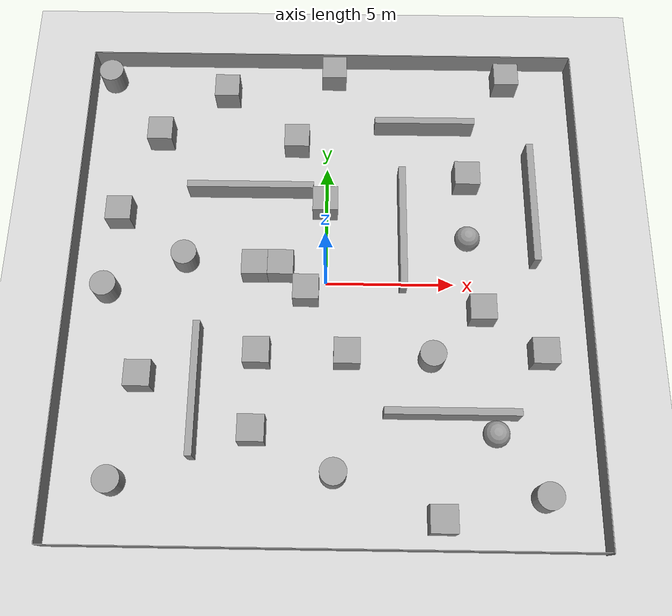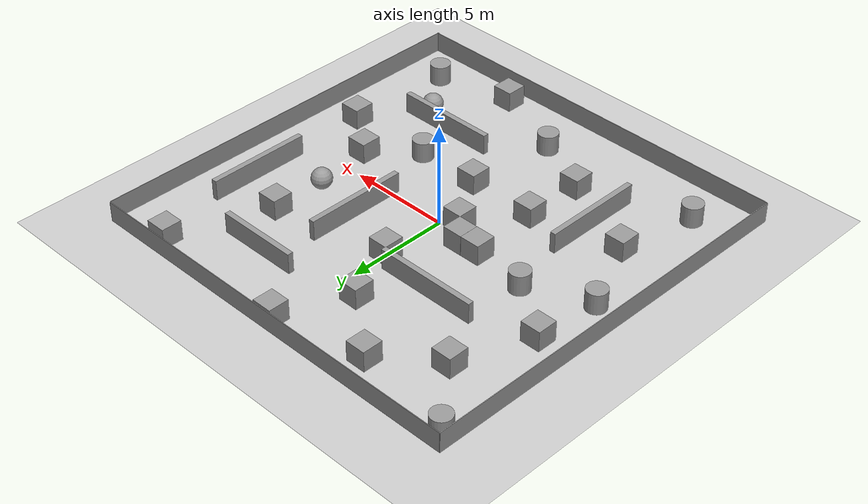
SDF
<sdf version="1.7">
 <world name="default">
  <light name="sun" type="directional">
   <pose>0 0 10 0 -0 0</pose>
   <diffuse>0.8 0.8 0.8 1</diffuse>
   <specular>0.2 0.2 0.2 1</specular>
   <attenuation>
    <range>1000</range>
    <constant>0.9</constant>
    <linear>0.01</linear>
    <quadratic>0.001</quadratic>
   </attenuation>
   <direction>-0.5 0.1 -0.9</direction>
   <spot><inner_angle>0</inner_angle><outer_angle>0</outer_angle><falloff>0</falloff></spot>
  </light>
  <model name="ground_plane">
   <static>1</static>
   <link name="link">
    <collision name="collision">
     <geometry><plane><normal>0 0 1</normal><size>100 100</size></plane></geometry>
     <surface>
      <contact><collide_bitmask>65535</collide_bitmask></contact>
      <friction><ode><mu>100</mu><mu2>50</mu2></ode></friction>
     </surface>
    </collision>
    <visual name="visual">
     <cast_shadows>0</cast_shadows>
     <geometry><plane><normal>0 0 1</normal><size>100 100</size></plane></geometry>
     <material>
      <script><uri>file://media/materials/scripts/gazebo.material</uri><name>Gazebo/Grey</name></script>
     </material>
    </visual>
   </link>
  </model>
  <gravity>0 0 -9.8</gravity>
  <magnetic_field>6e-06 2.3e-05 -4.2e-05</magnetic_field>
  <atmosphere type="adiabatic"/>
  <physics type="ode">
   <max_step_size>0.001</max_step_size>
   <real_time_factor>1</real_time_factor>
   <real_time_update_rate>1000</real_time_update_rate>
  </physics>
  <scene><ambient>0.4 0.4 0.4 1</ambient><background>0.7 0.7 0.7 1</background><shadows>1</shadows></scene>
  <spherical_coordinates>
   <surface_model>EARTH_WGS84</surface_model>
   <latitude_deg>0</latitude_deg>
   <longitude_deg>0</longitude_deg>
   <elevation>0</elevation>
   <heading_deg>0</heading_deg>
  </spherical_coordinates>
  <model name="m">
   <link name="link_0">
    <inertial>
     <mass>0.665554</mass>
     <inertia><ixx>0.0555244</ixx><ixy>0</ixy><ixz>0</ixz><iyy>22.0844</iyy><iyz>0</iyz><izz>22.029</izz></inertia>
    </inertial>
    <pose>0.242404 -11.0845 0 0 -0 0</pose>
    <visual name="visual">
     <geometry><box><size>19.9295 0.033323 1</size></box></geometry>
     <material>
      <lighting>1</lighting>
      <script><uri>file://media/materials/scripts/gazebo.material</uri><name>Gazebo/Grey</name></script>
      <shader type="pixel"><normal_map>__default__</normal_map></shader>
     </material>
    </visual>
    <collision name="collision">
     <geometry><box><size>19.9295 0.033323 1</size></box></geometry>
     <surface>
      <friction>
       <ode><mu>1</mu><mu2>1</mu2><fdir1>0 0 0</fdir1><slip1>0</slip1><slip2>0</slip2></ode>
       <torsional>
        <coefficient>1</coefficient>
        <patch_radius>0</patch_radius>
        <surface_radius>0</surface_radius>
        <use_patch_radius>1</use_patch_radius>
        <ode><slip>0</slip></ode>
       </torsional>
      </friction>
      <bounce><restitution_coefficient>0</restitution_coefficient><threshold>1e+06</threshold></bounce>
      <contact>
       <collide_without_contact>0</collide_without_contact>
       <collide_without_contact_bitmask>1</collide_without_contact_bitmask>
       <collide_bitmask>1</collide_bitmask>
       <ode>
        <soft_cfm>0</soft_cfm>
        <soft_erp>0.2</soft_erp>
        <kp>1e+13</kp>
        <kd>1</kd>
        <max_vel>0.01</max_vel>
        <min_depth>0</min_depth>
       </ode>
       <bullet>
        <split_impulse>1</split_impulse>
        <split_impulse_penetration_threshold>-0.01</split_impulse_penetration_threshold>
        <soft_cfm>0</soft_cfm>
        <soft_erp>0.2</soft_erp>
        <kp>1e+13</kp>
        <kd>1</kd>
       </bullet>
      </contact>
     </surface>
    </collision>
   </link>
   <link name="link_0_0">
    <inertial>
     <mass>1</mass>
     <inertia><ixx>0.145833</ixx><ixy>0</ixy><ixz>0</ixz><iyy>0.145833</iyy><iyz>0</iyz><izz>0.125</izz></inertia>
    </inertial>
    <pose>4.20277 -4.09935 -0.034602 -0.004806 1e-06 0</pose>
    <visual name="visual">
     <geometry><cylinder><radius>0.5</radius><length>1</length></cylinder></geometry>
     <material>
      <lighting>1</lighting>
      <script><uri>file://media/materials/scripts/gazebo.material</uri><name>Gazebo/Grey</name></script>
      <shader type="pixel"/>
     </material>
    </visual>
    <collision name="collision">
     <geometry><cylinder><radius>0.5</radius><length>1</length></cylinder></geometry>
     <surface>
      <friction>
       <ode><mu>1</mu><mu2>1</mu2><fdir1>0 0 0</fdir1><slip1>0</slip1><slip2>0</slip2></ode>
       <torsional>
        <coefficient>1</coefficient>
        <patch_radius>0</patch_radius>
        <surface_radius>0</surface_radius>
        <use_patch_radius>1</use_patch_radius>
        <ode><slip>0</slip></ode>
       </torsional>
      </friction>
      <bounce><restitution_coefficient>0</restitution_coefficient><threshold>1e+06</threshold></bounce>
      <contact>
       <collide_without_contact>0</collide_without_contact>
       <collide_without_contact_bitmask>1</collide_without_contact_bitmask>
       <collide_bitmask>1</collide_bitmask>
       <ode>
        <soft_cfm>0</soft_cfm>
        <soft_erp>0.2</soft_erp>
        <kp>1e+13</kp>
        <kd>1</kd>
        <max_vel>0.01</max_vel>
        <min_depth>0</min_depth>
       </ode>
       <bullet>
        <split_impulse>1</split_impulse>
        <split_impulse_penetration_threshold>-0.01</split_impulse_penetration_threshold>
        <soft_cfm>0</soft_cfm>
        <soft_erp>0.2</soft_erp>
        <kp>1e+13</kp>
        <kd>1</kd>
       </bullet>
      </contact>
     </surface>
    </collision>
   </link>
   <link name="link_0_1">
    <inertial>
     <mass>1</mass>
     <inertia><ixx>0.1</ixx><ixy>0</ixy><ixz>0</ixz><iyy>0.1</iyy><iyz>0</iyz><izz>0.1</izz></inertia>
    </inertial>
    <pose>6.45955 -6.99136 -0.015862 -0.00386 0 0</pose>
    <visual name="visual">
     <geometry><sphere><radius>0.5</radius></sphere></geometry>
     <material>
      <lighting>1</lighting>
      <script><uri>file://media/materials/scripts/gazebo.material</uri><name>Gazebo/Grey</name></script>
      <shader type="pixel"/>
     </material>
    </visual>
    <collision name="collision">
     <geometry><sphere><radius>0.5</radius></sphere></geometry>
     <surface>
      <friction>
       <ode><mu>1</mu><mu2>1</mu2><fdir1>0 0 0</fdir1><slip1>0</slip1><slip2>0</slip2></ode>
       <torsional>
        <coefficient>1</coefficient>
        <patch_radius>0</patch_radius>
        <surface_radius>0</surface_radius>
        <use_patch_radius>1</use_patch_radius>
        <ode><slip>0</slip></ode>
       </torsional>
      </friction>
      <bounce><restitution_coefficient>0</restitution_coefficient><threshold>1e+06</threshold></bounce>
      <contact>
       <collide_without_contact>0</collide_without_contact>
       <collide_without_contact_bitmask>1</collide_without_contact_bitmask>
       <collide_bitmask>1</collide_bitmask>
       <ode>
        <soft_cfm>0</soft_cfm>
        <soft_erp>0.2</soft_erp>
        <kp>1e+13</kp>
        <kd>1</kd>
        <max_vel>0.01</max_vel>
        <min_depth>0</min_depth>
       </ode>
       <bullet>
        <split_impulse>1</split_impulse>
        <split_impulse_penetration_threshold>-0.01</split_impulse_penetration_threshold>
        <soft_cfm>0</soft_cfm>
        <soft_erp>0.2</soft_erp>
        <kp>1e+13</kp>
        <kd>1</kd>
       </bullet>
      </contact>
     </surface>
    </collision>
   </link>
   <link name="link_0_clone">
    <inertial>
     <mass>0.665554</mass>
     <inertia><ixx>0.0555244</ixx><ixy>0</ixy><ixz>0</ixz><iyy>22.0844</iyy><iyz>0</iyz><izz>22.029</izz></inertia>
    </inertial>
    <pose>0.261289 8.83473 0 0 -0 0</pose>
    <visual name="visual">
     <geometry><box><size>19.9295 0.033323 1</size></box></geometry>
     <material>
      <lighting>1</lighting>
      <script><uri>file://media/materials/scripts/gazebo.material</uri><name>Gazebo/Grey</name></script>
      <shader type="pixel"><normal_map>__default__</normal_map></shader>
     </material>
    </visual>
    <collision name="collision">
     <geometry><box><size>19.9295 0.033323 1</size></box></geometry>
     <surface>
      <friction>
       <ode><mu>1</mu><mu2>1</mu2><fdir1>0 0 0</fdir1><slip1>0</slip1><slip2>0</slip2></ode>
       <torsional>
        <coefficient>1</coefficient>
        <patch_radius>0</patch_radius>
        <surface_radius>0</surface_radius>
        <use_patch_radius>1</use_patch_radius>
        <ode><slip>0</slip></ode>
       </torsional>
      </friction>
      <bounce><restitution_coefficient>0</restitution_coefficient><threshold>1e+06</threshold></bounce>
      <contact>
       <collide_without_contact>0</collide_without_contact>
       <collide_without_contact_bitmask>1</collide_without_contact_bitmask>
       <collide_bitmask>1</collide_bitmask>
       <ode>
        <soft_cfm>0</soft_cfm>
        <soft_erp>0.2</soft_erp>
        <kp>1e+13</kp>
        <kd>1</kd>
        <max_vel>0.01</max_vel>
        <min_depth>0</min_depth>
       </ode>
       <bullet>
        <split_impulse>1</split_impulse>
        <split_impulse_penetration_threshold>-0.01</split_impulse_penetration_threshold>
        <soft_cfm>0</soft_cfm>
        <soft_erp>0.2</soft_erp>
        <kp>1e+13</kp>
        <kd>1</kd>
       </bullet>
      </contact>
     </surface>
    </collision>
   </link>
   <link name="link_0_clone_0">
    <inertial>
     <mass>0.665554</mass>
     <inertia><ixx>0.0555244</ixx><ixy>0</ixy><ixz>0</ixz><iyy>22.0844</iyy><iyz>0</iyz><izz>22.029</izz></inertia>
    </inertial>
    <pose>10.2239 -1.16779 -0 0 0 -1.57281</pose>
    <visual name="visual">
     <geometry><box><size>19.9295 0.033323 1</size></box></geometry>
     <material>
      <lighting>1</lighting>
      <script><uri>file://media/materials/scripts/gazebo.material</uri><name>Gazebo/Grey</name></script>
      <shader type="pixel"><normal_map>__default__</normal_map></shader>
     </material>
    </visual>
    <collision name="collision">
     <geometry><box><size>19.9295 0.033323 1</size></box></geometry>
     <surface>
      <friction>
       <ode><mu>1</mu><mu2>1</mu2><fdir1>0 0 0</fdir1><slip1>0</slip1><slip2>0</slip2></ode>
       <torsional>
        <coefficient>1</coefficient>
        <patch_radius>0</patch_radius>
        <surface_radius>0</surface_radius>
        <use_patch_radius>1</use_patch_radius>
        <ode><slip>0</slip></ode>
       </torsional>
      </friction>
      <bounce><restitution_coefficient>0</restitution_coefficient><threshold>1e+06</threshold></bounce>
      <contact>
       <collide_without_contact>0</collide_without_contact>
       <collide_without_contact_bitmask>1</collide_without_contact_bitmask>
       <collide_bitmask>1</collide_bitmask>
       <ode>
        <soft_cfm>0</soft_cfm>
        <soft_erp>0.2</soft_erp>
        <kp>1e+13</kp>
        <kd>1</kd>
        <max_vel>0.01</max_vel>
        <min_depth>0</min_depth>
       </ode>
       <bullet>
        <split_impulse>1</split_impulse>
        <split_impulse_penetration_threshold>-0.01</split_impulse_penetration_threshold>
        <soft_cfm>0</soft_cfm>
        <soft_erp>0.2</soft_erp>
        <kp>1e+13</kp>
        <kd>1</kd>
       </bullet>
      </contact>
     </surface>
    </collision>
   </link>
   <link name="link_0_clone_0_clone">
    <inertial>
     <mass>0.665554</mass>
     <inertia><ixx>0.0555244</ixx><ixy>0</ixy><ixz>0</ixz><iyy>22.0844</iyy><iyz>0</iyz><izz>22.029</izz></inertia>
    </inertial>
    <pose>-9.73471 -1.11767 0 0 0 -1.57281</pose>
    <visual name="visual">
     <geometry><box><size>19.9295 0.033323 1</size></box></geometry>
     <material>
      <lighting>1</lighting>
      <script><uri>file://media/materials/scripts/gazebo.material</uri><name>Gazebo/Grey</name></script>
      <shader type="pixel"><normal_map>__default__</normal_map></shader>
     </material>
    </visual>
    <collision name="collision">
     <geometry><box><size>19.9295 0.033323 1</size></box></geometry>
     <surface>
      <friction>
       <ode><mu>1</mu><mu2>1</mu2><fdir1>0 0 0</fdir1><slip1>0</slip1><slip2>0</slip2></ode>
       <torsional>
        <coefficient>1</coefficient>
        <patch_radius>0</patch_radius>
        <surface_radius>0</surface_radius>
        <use_patch_radius>1</use_patch_radius>
        <ode><slip>0</slip></ode>
       </torsional>
      </friction>
      <bounce><restitution_coefficient>0</restitution_coefficient><threshold>1e+06</threshold></bounce>
      <contact>
       <collide_without_contact>0</collide_without_contact>
       <collide_without_contact_bitmask>1</collide_without_contact_bitmask>
       <collide_bitmask>1</collide_bitmask>
       <ode>
        <soft_cfm>0</soft_cfm>
        <soft_erp>0.2</soft_erp>
        <kp>1e+13</kp>
        <kd>1</kd>
        <max_vel>0.01</max_vel>
        <min_depth>0</min_depth>
       </ode>
       <bullet>
        <split_impulse>1</split_impulse>
        <split_impulse_penetration_threshold>-0.01</split_impulse_penetration_threshold>
        <soft_cfm>0</soft_cfm>
        <soft_erp>0.2</soft_erp>
        <kp>1e+13</kp>
        <kd>1</kd>
       </bullet>
      </contact>
     </surface>
    </collision>
   </link>
   <link name="link_1">
    <inertial>
     <mass>1.10085</mass>
     <inertia>
      <ixx>0.0985725</ixx>
      <ixy>0</ixy>
      <ixz>0</ixz>
      <iyy>1.60334</iyy>
      <iyz>0</iyz>
      <izz>1.51844</izz>
     </inertia>
    </inertial>
    <pose>4.09587 5.72765 -0.000749 0 -0 0</pose>
    <visual name="visual">
     <geometry><box><size>4.05924 0.272957 1</size></box></geometry>
     <material>
      <lighting>1</lighting>
      <script><uri>file://media/materials/scripts/gazebo.material</uri><name>Gazebo/Grey</name></script>
      <shader type="pixel"/>
     </material>
    </visual>
    <collision name="collision">
     <geometry><box><size>4.05924 0.272957 1</size></box></geometry>
     <surface>
      <friction>
       <ode><mu>1</mu><mu2>1</mu2><fdir1>0 0 0</fdir1><slip1>0</slip1><slip2>0</slip2></ode>
       <torsional>
        <coefficient>1</coefficient>
        <patch_radius>0</patch_radius>
        <surface_radius>0</surface_radius>
        <use_patch_radius>1</use_patch_radius>
        <ode><slip>0</slip></ode>
       </torsional>
      </friction>
      <bounce><restitution_coefficient>0</restitution_coefficient><threshold>1e+06</threshold></bounce>
      <contact>
       <collide_without_contact>0</collide_without_contact>
       <collide_without_contact_bitmask>1</collide_without_contact_bitmask>
       <collide_bitmask>1</collide_bitmask>
       <ode>
        <soft_cfm>0</soft_cfm>
        <soft_erp>0.2</soft_erp>
        <kp>1e+13</kp>
        <kd>1</kd>
        <max_vel>0.01</max_vel>
        <min_depth>0</min_depth>
       </ode>
       <bullet>
        <split_impulse>1</split_impulse>
        <split_impulse_penetration_threshold>-0.01</split_impulse_penetration_threshold>
        <soft_cfm>0</soft_cfm>
        <soft_erp>0.2</soft_erp>
        <kp>1e+13</kp>
        <kd>1</kd>
       </bullet>
      </contact>
     </surface>
    </collision>
   </link>
   <link name="link_10">
    <inertial>
     <mass>1</mass>
     <inertia>
      <ixx>0.166667</ixx>
      <ixy>0</ixy>
      <ixz>0</ixz>
      <iyy>0.166667</iyy>
      <iyz>0</iyz>
      <izz>0.166667</izz>
     </inertia>
    </inertial>
    <pose>8.39276 -3.93798 -0 0 -0 0</pose>
    <visual name="visual">
     <geometry><box><size>1 1 1</size></box></geometry>
     <material>
      <lighting>1</lighting>
      <script><uri>file://media/materials/scripts/gazebo.material</uri><name>Gazebo/Grey</name></script>
      <shader type="pixel"/>
     </material>
    </visual>
    <collision name="collision">
     <geometry><box><size>1 1 1</size></box></geometry>
     <surface>
      <friction>
       <ode><mu>1</mu><mu2>1</mu2><fdir1>0 0 0</fdir1><slip1>0</slip1><slip2>0</slip2></ode>
       <torsional>
        <coefficient>1</coefficient>
        <patch_radius>0</patch_radius>
        <surface_radius>0</surface_radius>
        <use_patch_radius>1</use_patch_radius>
        <ode><slip>0</slip></ode>
       </torsional>
      </friction>
      <bounce><restitution_coefficient>0</restitution_coefficient><threshold>1e+06</threshold></bounce>
      <contact>
       <collide_without_contact>0</collide_without_contact>
       <collide_without_contact_bitmask>1</collide_without_contact_bitmask>
       <collide_bitmask>1</collide_bitmask>
       <ode>
        <soft_cfm>0</soft_cfm>
        <soft_erp>0.2</soft_erp>
        <kp>1e+13</kp>
        <kd>1</kd>
        <max_vel>0.01</max_vel>
        <min_depth>0</min_depth>
       </ode>
       <bullet>
        <split_impulse>1</split_impulse>
        <split_impulse_penetration_threshold>-0.01</split_impulse_penetration_threshold>
        <soft_cfm>0</soft_cfm>
        <soft_erp>0.2</soft_erp>
        <kp>1e+13</kp>
        <kd>1</kd>
       </bullet>
      </contact>
     </surface>
    </collision>
   </link>
   <link name="link_11">
    <inertial>
     <mass>1</mass>
     <inertia>
      <ixx>0.166667</ixx>
      <ixy>0</ixy>
      <ixz>0</ixz>
      <iyy>0.166667</iyy>
      <iyz>0</iyz>
      <izz>0.166667</izz>
     </inertia>
    </inertial>
    <pose>4.41334 -10.0358 0.006324 0 -0 0</pose>
    <visual name="visual">
     <geometry><box><size>1 1 1</size></box></geometry>
     <material>
      <lighting>1</lighting>
      <script><uri>file://media/materials/scripts/gazebo.material</uri><name>Gazebo/Grey</name></script>
      <shader type="pixel"/>
     </material>
    </visual>
    <collision name="collision">
     <geometry><box><size>1 1 1</size></box></geometry>
     <surface>
      <friction>
       <ode><mu>1</mu><mu2>1</mu2><fdir1>0 0 0</fdir1><slip1>0</slip1><slip2>0</slip2></ode>
       <torsional>
        <coefficient>1</coefficient>
        <patch_radius>0</patch_radius>
        <surface_radius>0</surface_radius>
        <use_patch_radius>1</use_patch_radius>
        <ode><slip>0</slip></ode>
       </torsional>
      </friction>
      <bounce><restitution_coefficient>0</restitution_coefficient><threshold>1e+06</threshold></bounce>
      <contact>
       <collide_without_contact>0</collide_without_contact>
       <collide_without_contact_bitmask>1</collide_without_contact_bitmask>
       <collide_bitmask>1</collide_bitmask>
       <ode>
        <soft_cfm>0</soft_cfm>
        <soft_erp>0.2</soft_erp>
        <kp>1e+13</kp>
        <kd>1</kd>
        <max_vel>0.01</max_vel>
        <min_depth>0</min_depth>
       </ode>
       <bullet>
        <split_impulse>1</split_impulse>
        <split_impulse_penetration_threshold>-0.01</split_impulse_penetration_threshold>
        <soft_cfm>0</soft_cfm>
        <soft_erp>0.2</soft_erp>
        <kp>1e+13</kp>
        <kd>1</kd>
       </bullet>
      </contact>
     </surface>
    </collision>
   </link>
   <link name="link_12">
    <inertial>
     <mass>1</mass>
     <inertia>
      <ixx>0.166667</ixx>
      <ixy>0</ixy>
      <ixz>0</ixz>
      <iyy>0.166667</iyy>
      <iyz>0</iyz>
      <izz>0.166667</izz>
     </inertia>
    </inertial>
    <pose>0.990011 -4.03824 0 0 -0 0</pose>
    <visual name="visual">
     <geometry><box><size>1 1 1</size></box></geometry>
     <material>
      <lighting>1</lighting>
      <script><uri>file://media/materials/scripts/gazebo.material</uri><name>Gazebo/Grey</name></script>
      <shader type="pixel"/>
     </material>
    </visual>
    <collision name="collision">
     <geometry><box><size>1 1 1</size></box></geometry>
     <surface>
      <friction>
       <ode><mu>1</mu><mu2>1</mu2><fdir1>0 0 0</fdir1><slip1>0</slip1><slip2>0</slip2></ode>
       <torsional>
        <coefficient>1</coefficient>
        <patch_radius>0</patch_radius>
        <surface_radius>0</surface_radius>
        <use_patch_radius>1</use_patch_radius>
        <ode><slip>0</slip></ode>
       </torsional>
      </friction>
      <bounce><restitution_coefficient>0</restitution_coefficient><threshold>1e+06</threshold></bounce>
      <contact>
       <collide_without_contact>0</collide_without_contact>
       <collide_without_contact_bitmask>1</collide_without_contact_bitmask>
       <collide_bitmask>1</collide_bitmask>
       <ode>
        <soft_cfm>0</soft_cfm>
        <soft_erp>0.2</soft_erp>
        <kp>1e+13</kp>
        <kd>1</kd>
        <max_vel>0.01</max_vel>
        <min_depth>0</min_depth>
       </ode>
       <bullet>
        <split_impulse>1</split_impulse>
        <split_impulse_penetration_threshold>-0.01</split_impulse_penetration_threshold>
        <soft_cfm>0</soft_cfm>
        <soft_erp>0.2</soft_erp>
        <kp>1e+13</kp>
        <kd>1</kd>
       </bullet>
      </contact>
     </surface>
    </collision>
   </link>
   <link name="link_12_clone">
    <inertial>
     <mass>1</mass>
     <inertia>
      <ixx>0.166667</ixx>
      <ixy>0</ixy>
      <ixz>0</ixz>
      <iyy>0.166667</iyy>
      <iyz>0</iyz>
      <izz>0.166667</izz>
     </inertia>
    </inertial>
    <pose>-2.46639 -6.9622 -0 0 -0 0</pose>
    <visual name="visual">
     <geometry><box><size>1 1 1</size></box></geometry>
     <material>
      <lighting>1</lighting>
      <script><uri>file://media/materials/scripts/gazebo.material</uri><name>Gazebo/Grey</name></script>
      <shader type="pixel"/>
     </material>
    </visual>
    <collision name="collision">
     <geometry><box><size>1 1 1</size></box></geometry>
     <surface>
      <friction>
       <ode><mu>1</mu><mu2>1</mu2><fdir1>0 0 0</fdir1><slip1>0</slip1><slip2>0</slip2></ode>
       <torsional>
        <coefficient>1</coefficient>
        <patch_radius>0</patch_radius>
        <surface_radius>0</surface_radius>
        <use_patch_radius>1</use_patch_radius>
        <ode><slip>0</slip></ode>
       </torsional>
      </friction>
      <bounce><restitution_coefficient>0</restitution_coefficient><threshold>1e+06</threshold></bounce>
      <contact>
       <collide_without_contact>0</collide_without_contact>
       <collide_without_contact_bitmask>1</collide_without_contact_bitmask>
       <collide_bitmask>1</collide_bitmask>
       <ode>
        <soft_cfm>0</soft_cfm>
        <soft_erp>0.2</soft_erp>
        <kp>1e+13</kp>
        <kd>1</kd>
        <max_vel>0.01</max_vel>
        <min_depth>0</min_depth>
       </ode>
       <bullet>
        <split_impulse>1</split_impulse>
        <split_impulse_penetration_threshold>-0.01</split_impulse_penetration_threshold>
        <soft_cfm>0</soft_cfm>
        <soft_erp>0.2</soft_erp>
        <kp>1e+13</kp>
        <kd>1</kd>
       </bullet>
      </contact>
     </surface>
    </collision>
   </link>
   <link name="link_13">
    <inertial>
     <mass>1</mass>
     <inertia><ixx>0.145833</ixx><ixy>0</ixy><ixz>0</ixz><iyy>0.145833</iyy><iyz>0</iyz><izz>0.125</izz></inertia>
    </inertial>
    <pose>-5.35505 -0.19432 -0 0 -0 0</pose>
    <visual name="visual">
     <geometry><cylinder><radius>0.5</radius><length>1</length></cylinder></geometry>
     <material>
      <lighting>1</lighting>
      <script><uri>file://media/materials/scripts/gazebo.material</uri><name>Gazebo/Grey</name></script>
      <shader type="pixel"/>
     </material>
    </visual>
    <collision name="collision">
     <geometry><cylinder><radius>0.5</radius><length>1</length></cylinder></geometry>
     <surface>
      <friction>
       <ode><mu>1</mu><mu2>1</mu2><fdir1>0 0 0</fdir1><slip1>0</slip1><slip2>0</slip2></ode>
       <torsional>
        <coefficient>1</coefficient>
        <patch_radius>0</patch_radius>
        <surface_radius>0</surface_radius>
        <use_patch_radius>1</use_patch_radius>
        <ode><slip>0</slip></ode>
       </torsional>
      </friction>
      <bounce><restitution_coefficient>0</restitution_coefficient><threshold>1e+06</threshold></bounce>
      <contact>
       <collide_without_contact>0</collide_without_contact>
       <collide_without_contact_bitmask>1</collide_without_contact_bitmask>
       <collide_bitmask>1</collide_bitmask>
       <ode>
        <soft_cfm>0</soft_cfm>
        <soft_erp>0.2</soft_erp>
        <kp>1e+13</kp>
        <kd>1</kd>
        <max_vel>0.01</max_vel>
        <min_depth>0</min_depth>
       </ode>
       <bullet>
        <split_impulse>1</split_impulse>
        <split_impulse_penetration_threshold>-0.01</split_impulse_penetration_threshold>
        <soft_cfm>0</soft_cfm>
        <soft_erp>0.2</soft_erp>
        <kp>1e+13</kp>
        <kd>1</kd>
       </bullet>
      </contact>
     </surface>
    </collision>
   </link>
   <link name="link_14">
    <inertial>
     <mass>1</mass>
     <inertia><ixx>0.145833</ixx><ixy>0</ixy><ixz>0</ixz><iyy>0.145833</iyy><iyz>0</iyz><izz>0.125</izz></inertia>
    </inertial>
    <pose>-8.3538 -1.5149 0 0 -0 0</pose>
    <visual name="visual">
     <geometry><cylinder><radius>0.5</radius><length>1</length></cylinder></geometry>
     <material>
      <lighting>1</lighting>
      <script><uri>file://media/materials/scripts/gazebo.material</uri><name>Gazebo/Grey</name></script>
      <shader type="pixel"/>
     </material>
    </visual>
    <collision name="collision">
     <geometry><cylinder><radius>0.5</radius><length>1</length></cylinder></geometry>
     <surface>
      <friction>
       <ode><mu>1</mu><mu2>1</mu2><fdir1>0 0 0</fdir1><slip1>0</slip1><slip2>0</slip2></ode>
       <torsional>
        <coefficient>1</coefficient>
        <patch_radius>0</patch_radius>
        <surface_radius>0</surface_radius>
        <use_patch_radius>1</use_patch_radius>
        <ode><slip>0</slip></ode>
       </torsional>
      </friction>
      <bounce><restitution_coefficient>0</restitution_coefficient><threshold>1e+06</threshold></bounce>
      <contact>
       <collide_without_contact>0</collide_without_contact>
       <collide_without_contact_bitmask>1</collide_without_contact_bitmask>
       <collide_bitmask>1</collide_bitmask>
       <ode>
        <soft_cfm>0</soft_cfm>
        <soft_erp>0.2</soft_erp>
        <kp>1e+13</kp>
        <kd>1</kd>
        <max_vel>0.01</max_vel>
        <min_depth>0</min_depth>
       </ode>
       <bullet>
        <split_impulse>1</split_impulse>
        <split_impulse_penetration_threshold>-0.01</split_impulse_penetration_threshold>
        <soft_cfm>0</soft_cfm>
        <soft_erp>0.2</soft_erp>
        <kp>1e+13</kp>
        <kd>1</kd>
       </bullet>
      </contact>
     </surface>
    </collision>
   </link>
   <link name="link_15">
    <inertial>
     <mass>1</mass>
     <inertia>
      <ixx>0.166667</ixx>
      <ixy>0</ixy>
      <ixz>0</ixz>
      <iyy>0.166667</iyy>
      <iyz>0</iyz>
      <izz>0.166667</izz>
     </inertia>
    </inertial>
    <pose>-6.73247 -4.99641 0.006202 0 -0 0</pose>
    <visual name="visual">
     <geometry><box><size>1 1 1</size></box></geometry>
     <material>
      <lighting>1</lighting>
      <script><uri>file://media/materials/scripts/gazebo.material</uri><name>Gazebo/Grey</name></script>
      <shader type="pixel"/>
     </material>
    </visual>
    <collision name="collision">
     <geometry><box><size>1 1 1</size></box></geometry>
     <surface>
      <friction>
       <ode><mu>1</mu><mu2>1</mu2><fdir1>0 0 0</fdir1><slip1>0</slip1><slip2>0</slip2></ode>
       <torsional>
        <coefficient>1</coefficient>
        <patch_radius>0</patch_radius>
        <surface_radius>0</surface_radius>
        <use_patch_radius>1</use_patch_radius>
        <ode><slip>0</slip></ode>
       </torsional>
      </friction>
      <bounce><restitution_coefficient>0</restitution_coefficient><threshold>1e+06</threshold></bounce>
      <contact>
       <collide_without_contact>0</collide_without_contact>
       <collide_without_contact_bitmask>1</collide_without_contact_bitmask>
       <collide_bitmask>1</collide_bitmask>
       <ode>
        <soft_cfm>0</soft_cfm>
        <soft_erp>0.2</soft_erp>
        <kp>1e+13</kp>
        <kd>1</kd>
        <max_vel>0.01</max_vel>
        <min_depth>0</min_depth>
       </ode>
       <bullet>
        <split_impulse>1</split_impulse>
        <split_impulse_penetration_threshold>-0.01</split_impulse_penetration_threshold>
        <soft_cfm>0</soft_cfm>
        <soft_erp>0.2</soft_erp>
        <kp>1e+13</kp>
        <kd>1</kd>
       </bullet>
      </contact>
     </surface>
    </collision>
   </link>
   <link name="link_16">
    <inertial>
     <mass>1</mass>
     <inertia>
      <ixx>0.166667</ixx>
      <ixy>0</ixy>
      <ixz>0</ixz>
      <iyy>0.166667</iyy>
      <iyz>0</iyz>
      <izz>0.166667</izz>
     </inertia>
    </inertial>
    <pose>0.092071 2.17183 -0 0 -0 0</pose>
    <visual name="visual">
     <geometry><box><size>1 1 1</size></box></geometry>
     <material>
      <lighting>1</lighting>
      <script><uri>file://media/materials/scripts/gazebo.material</uri><name>Gazebo/Grey</name></script>
      <shader type="pixel"/>
     </material>
    </visual>
    <collision name="collision">
     <geometry><box><size>1 1 1</size></box></geometry>
     <surface>
      <friction>
       <ode><mu>1</mu><mu2>1</mu2><fdir1>0 0 0</fdir1><slip1>0</slip1><slip2>0</slip2></ode>
       <torsional>
        <coefficient>1</coefficient>
        <patch_radius>0</patch_radius>
        <surface_radius>0</surface_radius>
        <use_patch_radius>1</use_patch_radius>
        <ode><slip>0</slip></ode>
       </torsional>
      </friction>
      <bounce><restitution_coefficient>0</restitution_coefficient><threshold>1e+06</threshold></bounce>
      <contact>
       <collide_without_contact>0</collide_without_contact>
       <collide_without_contact_bitmask>1</collide_without_contact_bitmask>
       <collide_bitmask>1</collide_bitmask>
       <ode>
        <soft_cfm>0</soft_cfm>
        <soft_erp>0.2</soft_erp>
        <kp>1e+13</kp>
        <kd>1</kd>
        <max_vel>0.01</max_vel>
        <min_depth>0</min_depth>
       </ode>
       <bullet>
        <split_impulse>1</split_impulse>
        <split_impulse_penetration_threshold>-0.01</split_impulse_penetration_threshold>
        <soft_cfm>0</soft_cfm>
        <soft_erp>0.2</soft_erp>
        <kp>1e+13</kp>
        <kd>1</kd>
       </bullet>
      </contact>
     </surface>
    </collision>
   </link>
   <link name="link_17">
    <inertial>
     <mass>1</mass>
     <inertia>
      <ixx>0.166667</ixx>
      <ixy>0</ixy>
      <ixz>0</ixz>
      <iyy>0.166667</iyy>
      <iyz>0</iyz>
      <izz>0.166667</izz>
     </inertia>
    </inertial>
    <pose>-1.59709 -0.551127 0 0 -0 0</pose>
    <visual name="visual">
     <geometry><box><size>1 1 1</size></box></geometry>
     <material>
      <lighting>1</lighting>
      <script><uri>file://media/materials/scripts/gazebo.material</uri><name>Gazebo/Grey</name></script>
      <shader type="pixel"/>
     </material>
    </visual>
    <collision name="collision">
     <geometry><box><size>1 1 1</size></box></geometry>
     <surface>
      <friction>
       <ode><mu>1</mu><mu2>1</mu2><fdir1>0 0 0</fdir1><slip1>0</slip1><slip2>0</slip2></ode>
       <torsional>
        <coefficient>1</coefficient>
        <patch_radius>0</patch_radius>
        <surface_radius>0</surface_radius>
        <use_patch_radius>1</use_patch_radius>
        <ode><slip>0</slip></ode>
       </torsional>
      </friction>
      <bounce><restitution_coefficient>0</restitution_coefficient><threshold>1e+06</threshold></bounce>
      <contact>
       <collide_without_contact>0</collide_without_contact>
       <collide_without_contact_bitmask>1</collide_without_contact_bitmask>
       <collide_bitmask>1</collide_bitmask>
       <ode>
        <soft_cfm>0</soft_cfm>
        <soft_erp>0.2</soft_erp>
        <kp>1e+13</kp>
        <kd>1</kd>
        <max_vel>0.01</max_vel>
        <min_depth>0</min_depth>
       </ode>
       <bullet>
        <split_impulse>1</split_impulse>
        <split_impulse_penetration_threshold>-0.01</split_impulse_penetration_threshold>
        <soft_cfm>0</soft_cfm>
        <soft_erp>0.2</soft_erp>
        <kp>1e+13</kp>
        <kd>1</kd>
       </bullet>
      </contact>
     </surface>
    </collision>
   </link>
   <link name="link_18">
    <inertial>
     <mass>1</mass>
     <inertia>
      <ixx>0.166667</ixx>
      <ixy>0</ixy>
      <ixz>0</ixz>
      <iyy>0.166667</iyy>
      <iyz>0</iyz>
      <izz>0.166667</izz>
     </inertia>
    </inertial>
    <pose>-0.60758 -1.54069 -0 0 -0 0</pose>
    <visual name="visual">
     <geometry><box><size>1 1 1</size></box></geometry>
     <material>
      <lighting>1</lighting>
      <script><uri>file://media/materials/scripts/gazebo.material</uri><name>Gazebo/Grey</name></script>
      <shader type="pixel"/>
     </material>
    </visual>
    <collision name="collision">
     <geometry><box><size>1 1 1</size></box></geometry>
     <surface>
      <friction>
       <ode><mu>1</mu><mu2>1</mu2><fdir1>0 0 0</fdir1><slip1>0</slip1><slip2>0</slip2></ode>
       <torsional>
        <coefficient>1</coefficient>
        <patch_radius>0</patch_radius>
        <surface_radius>0</surface_radius>
        <use_patch_radius>1</use_patch_radius>
        <ode><slip>0</slip></ode>
       </torsional>
      </friction>
      <bounce><restitution_coefficient>0</restitution_coefficient><threshold>1e+06</threshold></bounce>
      <contact>
       <collide_without_contact>0</collide_without_contact>
       <collide_without_contact_bitmask>1</collide_without_contact_bitmask>
       <collide_bitmask>1</collide_bitmask>
       <ode>
        <soft_cfm>0</soft_cfm>
        <soft_erp>0.2</soft_erp>
        <kp>1e+13</kp>
        <kd>1</kd>
        <max_vel>0.01</max_vel>
        <min_depth>0</min_depth>
       </ode>
       <bullet>
        <split_impulse>1</split_impulse>
        <split_impulse_penetration_threshold>-0.01</split_impulse_penetration_threshold>
        <soft_cfm>0</soft_cfm>
        <soft_erp>0.2</soft_erp>
        <kp>1e+13</kp>
        <kd>1</kd>
       </bullet>
      </contact>
     </surface>
    </collision>
   </link>
   <link name="link_19">
    <inertial>
     <mass>1</mass>
     <inertia>
      <ixx>0.166667</ixx>
      <ixy>0</ixy>
      <ixz>0</ixz>
      <iyy>0.166667</iyy>
      <iyz>0</iyz>
      <izz>0.166667</izz>
     </inertia>
    </inertial>
    <pose>-2.59814 -0.556156 -8.7e-05 0 -0 0</pose>
    <visual name="visual">
     <geometry><box><size>1 1 1</size></box></geometry>
     <material>
      <lighting>1</lighting>
      <script><uri>file://media/materials/scripts/gazebo.material</uri><name>Gazebo/Grey</name></script>
      <shader type="pixel"/>
     </material>
    </visual>
    <collision name="collision">
     <geometry><box><size>1 1 1</size></box></geometry>
     <surface>
      <friction>
       <ode><mu>1</mu><mu2>1</mu2><fdir1>0 0 0</fdir1><slip1>0</slip1><slip2>0</slip2></ode>
       <torsional>
        <coefficient>1</coefficient>
        <patch_radius>0</patch_radius>
        <surface_radius>0</surface_radius>
        <use_patch_radius>1</use_patch_radius>
        <ode><slip>0</slip></ode>
       </torsional>
      </friction>
      <bounce><restitution_coefficient>0</restitution_coefficient><threshold>1e+06</threshold></bounce>
      <contact>
       <collide_without_contact>0</collide_without_contact>
       <collide_without_contact_bitmask>1</collide_without_contact_bitmask>
       <collide_bitmask>1</collide_bitmask>
       <ode>
        <soft_cfm>0</soft_cfm>
        <soft_erp>0.2</soft_erp>
        <kp>1e+13</kp>
        <kd>1</kd>
        <max_vel>0.01</max_vel>
        <min_depth>0</min_depth>
       </ode>
       <bullet>
        <split_impulse>1</split_impulse>
        <split_impulse_penetration_threshold>-0.01</split_impulse_penetration_threshold>
        <soft_cfm>0</soft_cfm>
        <soft_erp>0.2</soft_erp>
        <kp>1e+13</kp>
        <kd>1</kd>
       </bullet>
      </contact>
     </surface>
    </collision>
   </link>
   <link name="link_1_0">
    <inertial>
     <mass>1</mass>
     <inertia><ixx>0.145833</ixx><ixy>0</ixy><ixz>0</ixz><iyy>0.145833</iyy><iyz>0</iyz><izz>0.125</izz></inertia>
    </inertial>
    <pose>0.527383 -8.46897 -0.01263 -0.004806 1e-06 0</pose>
    <visual name="visual">
     <geometry><cylinder><radius>0.5</radius><length>1</length></cylinder></geometry>
     <material>
      <lighting>1</lighting>
      <script><uri>file://media/materials/scripts/gazebo.material</uri><name>Gazebo/Grey</name></script>
      <shader type="pixel"/>
     </material>
    </visual>
    <collision name="collision">
     <geometry><cylinder><radius>0.5</radius><length>1</length></cylinder></geometry>
     <surface>
      <friction>
       <ode><mu>1</mu><mu2>1</mu2><fdir1>0 0 0</fdir1><slip1>0</slip1><slip2>0</slip2></ode>
       <torsional>
        <coefficient>1</coefficient>
        <patch_radius>0</patch_radius>
        <surface_radius>0</surface_radius>
        <use_patch_radius>1</use_patch_radius>
        <ode><slip>0</slip></ode>
       </torsional>
      </friction>
      <bounce><restitution_coefficient>0</restitution_coefficient><threshold>1e+06</threshold></bounce>
      <contact>
       <collide_without_contact>0</collide_without_contact>
       <collide_without_contact_bitmask>1</collide_without_contact_bitmask>
       <collide_bitmask>1</collide_bitmask>
       <ode>
        <soft_cfm>0</soft_cfm>
        <soft_erp>0.2</soft_erp>
        <kp>1e+13</kp>
        <kd>1</kd>
        <max_vel>0.01</max_vel>
        <min_depth>0</min_depth>
       </ode>
       <bullet>
        <split_impulse>1</split_impulse>
        <split_impulse_penetration_threshold>-0.01</split_impulse_penetration_threshold>
        <soft_cfm>0</soft_cfm>
        <soft_erp>0.2</soft_erp>
        <kp>1e+13</kp>
        <kd>1</kd>
       </bullet>
      </contact>
     </surface>
    </collision>
   </link>
   <link name="link_1_1">
    <inertial>
     <mass>1</mass>
     <inertia><ixx>0.145833</ixx><ixy>0</ixy><ixz>0</ixz><iyy>0.145833</iyy><iyz>0</iyz><izz>0.125</izz></inertia>
    </inertial>
    <pose>8.17297 -9.21008 -0.018715 -0.00838 0 0</pose>
    <visual name="visual">
     <geometry><cylinder><radius>0.5</radius><length>1</length></cylinder></geometry>
     <material>
      <lighting>1</lighting>
      <script><uri>file://media/materials/scripts/gazebo.material</uri><name>Gazebo/Grey</name></script>
      <shader type="pixel"/>
     </material>
    </visual>
    <collision name="collision">
     <geometry><cylinder><radius>0.5</radius><length>1</length></cylinder></geometry>
     <surface>
      <friction>
       <ode><mu>1</mu><mu2>1</mu2><fdir1>0 0 0</fdir1><slip1>0</slip1><slip2>0</slip2></ode>
       <torsional>
        <coefficient>1</coefficient>
        <patch_radius>0</patch_radius>
        <surface_radius>0</surface_radius>
        <use_patch_radius>1</use_patch_radius>
        <ode><slip>0</slip></ode>
       </torsional>
      </friction>
      <bounce><restitution_coefficient>0</restitution_coefficient><threshold>1e+06</threshold></bounce>
      <contact>
       <collide_without_contact>0</collide_without_contact>
       <collide_without_contact_bitmask>1</collide_without_contact_bitmask>
       <collide_bitmask>1</collide_bitmask>
       <ode>
        <soft_cfm>0</soft_cfm>
        <soft_erp>0.2</soft_erp>
        <kp>1e+13</kp>
        <kd>1</kd>
        <max_vel>0.01</max_vel>
        <min_depth>0</min_depth>
       </ode>
       <bullet>
        <split_impulse>1</split_impulse>
        <split_impulse_penetration_threshold>-0.01</split_impulse_penetration_threshold>
        <soft_cfm>0</soft_cfm>
        <soft_erp>0.2</soft_erp>
        <kp>1e+13</kp>
        <kd>1</kd>
       </bullet>
      </contact>
     </surface>
    </collision>
   </link>
   <link name="link_1_2">
    <inertial>
     <mass>1</mass>
     <inertia><ixx>0.145833</ixx><ixy>0</ixy><ixz>0</ixz><iyy>0.145833</iyy><iyz>0</iyz><izz>0.125</izz></inertia>
    </inertial>
    <pose>-8.97748 8.01226 -0.073784 -0.00386 0 0</pose>
    <visual name="visual">
     <geometry><cylinder><radius>0.5</radius><length>1</length></cylinder></geometry>
     <material>
      <lighting>1</lighting>
      <script><uri>file://media/materials/scripts/gazebo.material</uri><name>Gazebo/Grey</name></script>
      <shader type="pixel"/>
     </material>
    </visual>
    <collision name="collision">
     <geometry><cylinder><radius>0.5</radius><length>1</length></cylinder></geometry>
     <surface>
      <friction>
       <ode><mu>1</mu><mu2>1</mu2><fdir1>0 0 0</fdir1><slip1>0</slip1><slip2>0</slip2></ode>
       <torsional>
        <coefficient>1</coefficient>
        <patch_radius>0</patch_radius>
        <surface_radius>0</surface_radius>
        <use_patch_radius>1</use_patch_radius>
        <ode><slip>0</slip></ode>
       </torsional>
      </friction>
      <bounce><restitution_coefficient>0</restitution_coefficient><threshold>1e+06</threshold></bounce>
      <contact>
       <collide_without_contact>0</collide_without_contact>
       <collide_without_contact_bitmask>1</collide_without_contact_bitmask>
       <collide_bitmask>1</collide_bitmask>
       <ode>
        <soft_cfm>0</soft_cfm>
        <soft_erp>0.2</soft_erp>
        <kp>1e+13</kp>
        <kd>1</kd>
        <max_vel>0.01</max_vel>
        <min_depth>0</min_depth>
       </ode>
       <bullet>
        <split_impulse>1</split_impulse>
        <split_impulse_penetration_threshold>-0.01</split_impulse_penetration_threshold>
        <soft_cfm>0</soft_cfm>
        <soft_erp>0.2</soft_erp>
        <kp>1e+13</kp>
        <kd>1</kd>
       </bullet>
      </contact>
     </surface>
    </collision>
   </link>
   <link name="link_1_clone">
    <inertial>
     <mass>1.36399</mass>
     <inertia><ixx>0.122135</ixx><ixy>0</ixy><ixz>0</ixz><iyy>2.98899</iyy><iyz>0</iyz><izz>2.88379</izz></inertia>
    </inertial>
    <pose>-2.8992 2.7445 -0 0 -0 0</pose>
    <visual name="visual">
     <geometry><box><size>5.02953 0.272957 1</size></box></geometry>
     <material>
      <lighting>1</lighting>
      <script><uri>file://media/materials/scripts/gazebo.material</uri><name>Gazebo/Grey</name></script>
      <shader type="pixel"/>
     </material>
    </visual>
    <collision name="collision">
     <geometry><box><size>5.02953 0.272957 1</size></box></geometry>
     <surface>
      <friction>
       <ode><mu>1</mu><mu2>1</mu2><fdir1>0 0 0</fdir1><slip1>0</slip1><slip2>0</slip2></ode>
       <torsional>
        <coefficient>1</coefficient>
        <patch_radius>0</patch_radius>
        <surface_radius>0</surface_radius>
        <use_patch_radius>1</use_patch_radius>
        <ode><slip>0</slip></ode>
       </torsional>
      </friction>
      <bounce><restitution_coefficient>0</restitution_coefficient><threshold>1e+06</threshold></bounce>
      <contact>
       <collide_without_contact>0</collide_without_contact>
       <collide_without_contact_bitmask>1</collide_without_contact_bitmask>
       <collide_bitmask>1</collide_bitmask>
       <ode>
        <soft_cfm>0</soft_cfm>
        <soft_erp>0.2</soft_erp>
        <kp>1e+13</kp>
        <kd>1</kd>
        <max_vel>0.01</max_vel>
        <min_depth>0</min_depth>
       </ode>
       <bullet>
        <split_impulse>1</split_impulse>
        <split_impulse_penetration_threshold>-0.01</split_impulse_penetration_threshold>
        <soft_cfm>0</soft_cfm>
        <soft_erp>0.2</soft_erp>
        <kp>1e+13</kp>
        <kd>1</kd>
       </bullet>
      </contact>
     </surface>
    </collision>
   </link>
   <link name="link_1_clone_0">
    <inertial>
     <mass>1.36399</mass>
     <inertia><ixx>0.122135</ixx><ixy>0</ixy><ixz>0</ixz><iyy>2.98899</iyy><iyz>0</iyz><izz>2.88379</izz></inertia>
    </inertial>
    <pose>4.85556 -6.26718 0 0 -0 0</pose>
    <visual name="visual">
     <geometry><box><size>5.02953 0.272957 1</size></box></geometry>
     <material>
      <lighting>1</lighting>
      <script><uri>file://media/materials/scripts/gazebo.material</uri><name>Gazebo/Grey</name></script>
      <shader type="pixel"/>
     </material>
    </visual>
    <collision name="collision">
     <geometry><box><size>5.02953 0.272957 1</size></box></geometry>
     <surface>
      <friction>
       <ode><mu>1</mu><mu2>1</mu2><fdir1>0 0 0</fdir1><slip1>0</slip1><slip2>0</slip2></ode>
       <torsional>
        <coefficient>1</coefficient>
        <patch_radius>0</patch_radius>
        <surface_radius>0</surface_radius>
        <use_patch_radius>1</use_patch_radius>
        <ode><slip>0</slip></ode>
       </torsional>
      </friction>
      <bounce><restitution_coefficient>0</restitution_coefficient><threshold>1e+06</threshold></bounce>
      <contact>
       <collide_without_contact>0</collide_without_contact>
       <collide_without_contact_bitmask>1</collide_without_contact_bitmask>
       <collide_bitmask>1</collide_bitmask>
       <ode>
        <soft_cfm>0</soft_cfm>
        <soft_erp>0.2</soft_erp>
        <kp>1e+13</kp>
        <kd>1</kd>
        <max_vel>0.01</max_vel>
        <min_depth>0</min_depth>
       </ode>
       <bullet>
        <split_impulse>1</split_impulse>
        <split_impulse_penetration_threshold>-0.01</split_impulse_penetration_threshold>
        <soft_cfm>0</soft_cfm>
        <soft_erp>0.2</soft_erp>
        <kp>1e+13</kp>
        <kd>1</kd>
       </bullet>
      </contact>
     </surface>
    </collision>
   </link>
   <link name="link_1_clone_0_clone">
    <inertial>
     <mass>1.36399</mass>
     <inertia><ixx>0.122135</ixx><ixy>0</ixy><ixz>0</ixz><iyy>2.98899</iyy><iyz>0</iyz><izz>2.88379</izz></inertia>
    </inertial>
    <pose>3.15146 1.09668 -0.009526 0 -0 1.57365</pose>
    <visual name="visual">
     <geometry><box><size>5.02953 0.272957 1</size></box></geometry>
     <material>
      <lighting>1</lighting>
      <script><uri>file://media/materials/scripts/gazebo.material</uri><name>Gazebo/Grey</name></script>
      <shader type="pixel"/>
     </material>
    </visual>
    <collision name="collision">
     <geometry><box><size>5.02953 0.272957 1</size></box></geometry>
     <surface>
      <friction>
       <ode><mu>1</mu><mu2>1</mu2><fdir1>0 0 0</fdir1><slip1>0</slip1><slip2>0</slip2></ode>
       <torsional>
        <coefficient>1</coefficient>
        <patch_radius>0</patch_radius>
        <surface_radius>0</surface_radius>
        <use_patch_radius>1</use_patch_radius>
        <ode><slip>0</slip></ode>
       </torsional>
      </friction>
      <bounce><restitution_coefficient>0</restitution_coefficient><threshold>1e+06</threshold></bounce>
      <contact>
       <collide_without_contact>0</collide_without_contact>
       <collide_without_contact_bitmask>1</collide_without_contact_bitmask>
       <collide_bitmask>1</collide_bitmask>
       <ode>
        <soft_cfm>0</soft_cfm>
        <soft_erp>0.2</soft_erp>
        <kp>1e+13</kp>
        <kd>1</kd>
        <max_vel>0.01</max_vel>
        <min_depth>0</min_depth>
       </ode>
       <bullet>
        <split_impulse>1</split_impulse>
        <split_impulse_penetration_threshold>-0.01</split_impulse_penetration_threshold>
        <soft_cfm>0</soft_cfm>
        <soft_erp>0.2</soft_erp>
        <kp>1e+13</kp>
        <kd>1</kd>
       </bullet>
      </contact>
     </surface>
    </collision>
   </link>
   <link name="link_1_clone_0_clone_clone">
    <inertial>
     <mass>1.36399</mass>
     <inertia><ixx>0.122135</ixx><ixy>0</ixy><ixz>0</ixz><iyy>2.98899</iyy><iyz>0</iyz><izz>2.88379</izz></inertia>
    </inertial>
    <pose>8.31243 2.17568 0.002399 0 -0 1.57366</pose>
    <visual name="visual">
     <geometry><box><size>5.02953 0.272957 1</size></box></geometry>
     <material>
      <lighting>1</lighting>
      <script><uri>file://media/materials/scripts/gazebo.material</uri><name>Gazebo/Grey</name></script>
      <shader type="pixel"/>
     </material>
    </visual>
    <collision name="collision">
     <geometry><box><size>5.02953 0.272957 1</size></box></geometry>
     <surface>
      <friction>
       <ode><mu>1</mu><mu2>1</mu2><fdir1>0 0 0</fdir1><slip1>0</slip1><slip2>0</slip2></ode>
       <torsional>
        <coefficient>1</coefficient>
        <patch_radius>0</patch_radius>
        <surface_radius>0</surface_radius>
        <use_patch_radius>1</use_patch_radius>
        <ode><slip>0</slip></ode>
       </torsional>
      </friction>
      <bounce><restitution_coefficient>0</restitution_coefficient><threshold>1e+06</threshold></bounce>
      <contact>
       <collide_without_contact>0</collide_without_contact>
       <collide_without_contact_bitmask>1</collide_without_contact_bitmask>
       <collide_bitmask>1</collide_bitmask>
       <ode>
        <soft_cfm>0</soft_cfm>
        <soft_erp>0.2</soft_erp>
        <kp>1e+13</kp>
        <kd>1</kd>
        <max_vel>0.01</max_vel>
        <min_depth>0</min_depth>
       </ode>
       <bullet>
        <split_impulse>1</split_impulse>
        <split_impulse_penetration_threshold>-0.01</split_impulse_penetration_threshold>
        <soft_cfm>0</soft_cfm>
        <soft_erp>0.2</soft_erp>
        <kp>1e+13</kp>
        <kd>1</kd>
       </bullet>
      </contact>
     </surface>
    </collision>
   </link>
   <link name="link_1_clone_0_clone_clone_clone">
    <inertial>
     <mass>1.36399</mass>
     <inertia><ixx>0.122135</ixx><ixy>0</ixy><ixz>0</ixz><iyy>2.98899</iyy><iyz>0</iyz><izz>2.88379</izz></inertia>
    </inertial>
    <pose>-4.65491 -5.47844 0 0 -0 1.57366</pose>
    <visual name="visual">
     <geometry><box><size>5.02953 0.272957 1</size></box></geometry>
     <material>
      <lighting>1</lighting>
      <script><uri>file://media/materials/scripts/gazebo.material</uri><name>Gazebo/Grey</name></script>
      <shader type="pixel"/>
     </material>
    </visual>
    <collision name="collision">
     <geometry><box><size>5.02953 0.272957 1</size></box></geometry>
     <surface>
      <friction>
       <ode><mu>1</mu><mu2>1</mu2><fdir1>0 0 0</fdir1><slip1>0</slip1><slip2>0</slip2></ode>
       <torsional>
        <coefficient>1</coefficient>
        <patch_radius>0</patch_radius>
        <surface_radius>0</surface_radius>
        <use_patch_radius>1</use_patch_radius>
        <ode><slip>0</slip></ode>
       </torsional>
      </friction>
      <bounce><restitution_coefficient>0</restitution_coefficient><threshold>1e+06</threshold></bounce>
      <contact>
       <collide_without_contact>0</collide_without_contact>
       <collide_without_contact_bitmask>1</collide_without_contact_bitmask>
       <collide_bitmask>1</collide_bitmask>
       <ode>
        <soft_cfm>0</soft_cfm>
        <soft_erp>0.2</soft_erp>
        <kp>1e+13</kp>
        <kd>1</kd>
        <max_vel>0.01</max_vel>
        <min_depth>0</min_depth>
       </ode>
       <bullet>
        <split_impulse>1</split_impulse>
        <split_impulse_penetration_threshold>-0.01</split_impulse_penetration_threshold>
        <soft_cfm>0</soft_cfm>
        <soft_erp>0.2</soft_erp>
        <kp>1e+13</kp>
        <kd>1</kd>
       </bullet>
      </contact>
     </surface>
    </collision>
   </link>
   <link name="link_2">
    <inertial>
     <mass>1</mass>
     <inertia>
      <ixx>0.166667</ixx>
      <ixy>0</ixy>
      <ixz>0</ixz>
      <iyy>0.166667</iyy>
      <iyz>0</iyz>
      <izz>0.166667</izz>
     </inertia>
    </inertial>
    <pose>-6.69125 5.24709 0.000363 0 -0 0</pose>
    <visual name="visual">
     <geometry><box><size>1 1 1</size></box></geometry>
     <material>
      <lighting>1</lighting>
      <script><uri>file://media/materials/scripts/gazebo.material</uri><name>Gazebo/Grey</name></script>
      <shader type="pixel"><normal_map>__default__</normal_map></shader>
     </material>
    </visual>
    <collision name="collision">
     <geometry><box><size>1 1 1</size></box></geometry>
     <surface>
      <friction>
       <ode><mu>1</mu><mu2>1</mu2><fdir1>0 0 0</fdir1><slip1>0</slip1><slip2>0</slip2></ode>
       <torsional>
        <coefficient>1</coefficient>
        <patch_radius>0</patch_radius>
        <surface_radius>0</surface_radius>
        <use_patch_radius>1</use_patch_radius>
        <ode><slip>0</slip></ode>
       </torsional>
      </friction>
      <bounce><restitution_coefficient>0</restitution_coefficient><threshold>1e+06</threshold></bounce>
      <contact>
       <collide_without_contact>0</collide_without_contact>
       <collide_without_contact_bitmask>1</collide_without_contact_bitmask>
       <collide_bitmask>1</collide_bitmask>
       <ode>
        <soft_cfm>0</soft_cfm>
        <soft_erp>0.2</soft_erp>
        <kp>1e+13</kp>
        <kd>1</kd>
        <max_vel>0.01</max_vel>
        <min_depth>0</min_depth>
       </ode>
       <bullet>
        <split_impulse>1</split_impulse>
        <split_impulse_penetration_threshold>-0.01</split_impulse_penetration_threshold>
        <soft_cfm>0</soft_cfm>
        <soft_erp>0.2</soft_erp>
        <kp>1e+13</kp>
        <kd>1</kd>
       </bullet>
      </contact>
     </surface>
    </collision>
   </link>
   <link name="link_2_0">
    <inertial>
     <mass>1</mass>
     <inertia><ixx>0.145833</ixx><ixy>0</ixy><ixz>0</ixz><iyy>0.145833</iyy><iyz>0</iyz><izz>0.125</izz></inertia>
    </inertial>
    <pose>-7.48828 -8.83848 -0.011627 -0.004806 1e-06 0</pose>
    <visual name="visual">
     <geometry><cylinder><radius>0.5</radius><length>1</length></cylinder></geometry>
     <material>
      <lighting>1</lighting>
      <script><uri>file://media/materials/scripts/gazebo.material</uri><name>Gazebo/Grey</name></script>
      <shader type="pixel"/>
     </material>
    </visual>
    <collision name="collision">
     <geometry><cylinder><radius>0.5</radius><length>1</length></cylinder></geometry>
     <surface>
      <friction>
       <ode><mu>1</mu><mu2>1</mu2><fdir1>0 0 0</fdir1><slip1>0</slip1><slip2>0</slip2></ode>
       <torsional>
        <coefficient>1</coefficient>
        <patch_radius>0</patch_radius>
        <surface_radius>0</surface_radius>
        <use_patch_radius>1</use_patch_radius>
        <ode><slip>0</slip></ode>
       </torsional>
      </friction>
      <bounce><restitution_coefficient>0</restitution_coefficient><threshold>1e+06</threshold></bounce>
      <contact>
       <collide_without_contact>0</collide_without_contact>
       <collide_without_contact_bitmask>1</collide_without_contact_bitmask>
       <collide_bitmask>1</collide_bitmask>
       <ode>
        <soft_cfm>0</soft_cfm>
        <soft_erp>0.2</soft_erp>
        <kp>1e+13</kp>
        <kd>1</kd>
        <max_vel>0.01</max_vel>
        <min_depth>0</min_depth>
       </ode>
       <bullet>
        <split_impulse>1</split_impulse>
        <split_impulse_penetration_threshold>-0.01</split_impulse_penetration_threshold>
        <soft_cfm>0</soft_cfm>
        <soft_erp>0.2</soft_erp>
        <kp>1e+13</kp>
        <kd>1</kd>
       </bullet>
      </contact>
     </surface>
    </collision>
   </link>
   <link name="link_3">
    <inertial>
     <mass>1</mass>
     <inertia>
      <ixx>0.166667</ixx>
      <ixy>0</ixy>
      <ixz>0</ixz>
      <iyy>0.166667</iyy>
      <iyz>0</iyz>
      <izz>0.166667</izz>
     </inertia>
    </inertial>
    <pose>-4.05988 7.30851 -0.002959 0 -0 0</pose>
    <visual name="visual">
     <geometry><box><size>1 1 1</size></box></geometry>
     <material>
      <lighting>1</lighting>
      <script><uri>file://media/materials/scripts/gazebo.material</uri><name>Gazebo/Grey</name></script>
      <shader type="pixel"/>
     </material>
    </visual>
    <collision name="collision">
     <geometry><box><size>1 1 1</size></box></geometry>
     <surface>
      <friction>
       <ode><mu>1</mu><mu2>1</mu2><fdir1>0 0 0</fdir1><slip1>0</slip1><slip2>0</slip2></ode>
       <torsional>
        <coefficient>1</coefficient>
        <patch_radius>0</patch_radius>
        <surface_radius>0</surface_radius>
        <use_patch_radius>1</use_patch_radius>
        <ode><slip>0</slip></ode>
       </torsional>
      </friction>
      <bounce><restitution_coefficient>0</restitution_coefficient><threshold>1e+06</threshold></bounce>
      <contact>
       <collide_without_contact>0</collide_without_contact>
       <collide_without_contact_bitmask>1</collide_without_contact_bitmask>
       <collide_bitmask>1</collide_bitmask>
       <ode>
        <soft_cfm>0</soft_cfm>
        <soft_erp>0.2</soft_erp>
        <kp>1e+13</kp>
        <kd>1</kd>
        <max_vel>0.01</max_vel>
        <min_depth>0</min_depth>
       </ode>
       <bullet>
        <split_impulse>1</split_impulse>
        <split_impulse_penetration_threshold>-0.01</split_impulse_penetration_threshold>
        <soft_cfm>0</soft_cfm>
        <soft_erp>0.2</soft_erp>
        <kp>1e+13</kp>
        <kd>1</kd>
       </bullet>
      </contact>
     </surface>
    </collision>
   </link>
   <link name="link_3_0">
    <inertial>
     <mass>1</mass>
     <inertia>
      <ixx>0.166667</ixx>
      <ixy>0</ixy>
      <ixz>0</ixz>
      <iyy>0.166667</iyy>
      <iyz>0</iyz>
      <izz>0.166667</izz>
     </inertia>
    </inertial>
    <pose>-2.39736 -4.04043 -0.033908 -0.004806 1e-06 0</pose>
    <visual name="visual">
     <geometry><box><size>1 1 1</size></box></geometry>
     <material>
      <lighting>1</lighting>
      <script><uri>file://media/materials/scripts/gazebo.material</uri><name>Gazebo/Grey</name></script>
      <shader type="pixel"/>
     </material>
    </visual>
    <collision name="collision">
     <geometry><box><size>1 1 1</size></box></geometry>
     <surface>
      <friction>
       <ode><mu>1</mu><mu2>1</mu2><fdir1>0 0 0</fdir1><slip1>0</slip1><slip2>0</slip2></ode>
       <torsional>
        <coefficient>1</coefficient>
        <patch_radius>0</patch_radius>
        <surface_radius>0</surface_radius>
        <use_patch_radius>1</use_patch_radius>
        <ode><slip>0</slip></ode>
       </torsional>
      </friction>
      <bounce><restitution_coefficient>0</restitution_coefficient><threshold>1e+06</threshold></bounce>
      <contact>
       <collide_without_contact>0</collide_without_contact>
       <collide_without_contact_bitmask>1</collide_without_contact_bitmask>
       <collide_bitmask>1</collide_bitmask>
       <ode>
        <soft_cfm>0</soft_cfm>
        <soft_erp>0.2</soft_erp>
        <kp>1e+13</kp>
        <kd>1</kd>
        <max_vel>0.01</max_vel>
        <min_depth>0</min_depth>
       </ode>
       <bullet>
        <split_impulse>1</split_impulse>
        <split_impulse_penetration_threshold>-0.01</split_impulse_penetration_threshold>
        <soft_cfm>0</soft_cfm>
        <soft_erp>0.2</soft_erp>
        <kp>1e+13</kp>
        <kd>1</kd>
       </bullet>
      </contact>
     </surface>
    </collision>
   </link>
   <link name="link_4">
    <inertial>
     <mass>1</mass>
     <inertia>
      <ixx>0.166667</ixx>
      <ixy>0</ixy>
      <ixz>0</ixz>
      <iyy>0.166667</iyy>
      <iyz>0</iyz>
      <izz>0.166667</izz>
     </inertia>
    </inertial>
    <pose>-8.05296 1.65939 -0.00011 0 -0 0</pose>
    <visual name="visual">
     <geometry><box><size>1 1 1</size></box></geometry>
     <material>
      <lighting>1</lighting>
      <script><uri>file://media/materials/scripts/gazebo.material</uri><name>Gazebo/Grey</name></script>
      <shader type="pixel"/>
     </material>
    </visual>
    <collision name="collision">
     <geometry><box><size>1 1 1</size></box></geometry>
     <surface>
      <friction>
       <ode><mu>1</mu><mu2>1</mu2><fdir1>0 0 0</fdir1><slip1>0</slip1><slip2>0</slip2></ode>
       <torsional>
        <coefficient>1</coefficient>
        <patch_radius>0</patch_radius>
        <surface_radius>0</surface_radius>
        <use_patch_radius>1</use_patch_radius>
        <ode><slip>0</slip></ode>
       </torsional>
      </friction>
      <bounce><restitution_coefficient>0</restitution_coefficient><threshold>1e+06</threshold></bounce>
      <contact>
       <collide_without_contact>0</collide_without_contact>
       <collide_without_contact_bitmask>1</collide_without_contact_bitmask>
       <collide_bitmask>1</collide_bitmask>
       <ode>
        <soft_cfm>0</soft_cfm>
        <soft_erp>0.2</soft_erp>
        <kp>1e+13</kp>
        <kd>1</kd>
        <max_vel>0.01</max_vel>
        <min_depth>0</min_depth>
       </ode>
       <bullet>
        <split_impulse>1</split_impulse>
        <split_impulse_penetration_threshold>-0.01</split_impulse_penetration_threshold>
        <soft_cfm>0</soft_cfm>
        <soft_erp>0.2</soft_erp>
        <kp>1e+13</kp>
        <kd>1</kd>
       </bullet>
      </contact>
     </surface>
    </collision>
   </link>
   <link name="link_4_0">
    <inertial>
     <mass>1</mass>
     <inertia><ixx>0.1</ixx><ixy>0</ixy><ixz>0</ixz><iyy>0.1</iyy><iyz>0</iyz><izz>0.1</izz></inertia>
    </inertial>
    <pose>5.70846 0.722794 -0.05681 -0.004806 1e-06 0</pose>
    <visual name="visual">
     <geometry><sphere><radius>0.5</radius></sphere></geometry>
     <material>
      <lighting>1</lighting>
      <script><uri>file://media/materials/scripts/gazebo.material</uri><name>Gazebo/Grey</name></script>
      <shader type="pixel"/>
     </material>
    </visual>
    <collision name="collision">
     <geometry><sphere><radius>0.5</radius></sphere></geometry>
     <surface>
      <friction>
       <ode><mu>1</mu><mu2>1</mu2><fdir1>0 0 0</fdir1><slip1>0</slip1><slip2>0</slip2></ode>
       <torsional>
        <coefficient>1</coefficient>
        <patch_radius>0</patch_radius>
        <surface_radius>0</surface_radius>
        <use_patch_radius>1</use_patch_radius>
        <ode><slip>0</slip></ode>
       </torsional>
      </friction>
      <bounce><restitution_coefficient>0</restitution_coefficient><threshold>1e+06</threshold></bounce>
      <contact>
       <collide_without_contact>0</collide_without_contact>
       <collide_without_contact_bitmask>1</collide_without_contact_bitmask>
       <collide_bitmask>1</collide_bitmask>
       <ode>
        <soft_cfm>0</soft_cfm>
        <soft_erp>0.2</soft_erp>
        <kp>1e+13</kp>
        <kd>1</kd>
        <max_vel>0.01</max_vel>
        <min_depth>0</min_depth>
       </ode>
       <bullet>
        <split_impulse>1</split_impulse>
        <split_impulse_penetration_threshold>-0.01</split_impulse_penetration_threshold>
        <soft_cfm>0</soft_cfm>
        <soft_erp>0.2</soft_erp>
        <kp>1e+13</kp>
        <kd>1</kd>
       </bullet>
      </contact>
     </surface>
    </collision>
   </link>
   <link name="link_5">
    <inertial>
     <mass>1</mass>
     <inertia>
      <ixx>0.166667</ixx>
      <ixy>0</ixy>
      <ixz>0</ixz>
      <iyy>0.166667</iyy>
      <iyz>0</iyz>
      <izz>0.166667</izz>
     </inertia>
    </inertial>
    <pose>-1.10362 4.98196 -0 0 -0 0</pose>
    <visual name="visual">
     <geometry><box><size>1 1 1</size></box></geometry>
     <material>
      <lighting>1</lighting>
      <script><uri>file://media/materials/scripts/gazebo.material</uri><name>Gazebo/Grey</name></script>
      <shader type="pixel"/>
     </material>
    </visual>
    <collision name="collision">
     <geometry><box><size>1 1 1</size></box></geometry>
     <surface>
      <friction>
       <ode><mu>1</mu><mu2>1</mu2><fdir1>0 0 0</fdir1><slip1>0</slip1><slip2>0</slip2></ode>
       <torsional>
        <coefficient>1</coefficient>
        <patch_radius>0</patch_radius>
        <surface_radius>0</surface_radius>
        <use_patch_radius>1</use_patch_radius>
        <ode><slip>0</slip></ode>
       </torsional>
      </friction>
      <bounce><restitution_coefficient>0</restitution_coefficient><threshold>1e+06</threshold></bounce>
      <contact>
       <collide_without_contact>0</collide_without_contact>
       <collide_without_contact_bitmask>1</collide_without_contact_bitmask>
       <collide_bitmask>1</collide_bitmask>
       <ode>
        <soft_cfm>0</soft_cfm>
        <soft_erp>0.2</soft_erp>
        <kp>1e+13</kp>
        <kd>1</kd>
        <max_vel>0.01</max_vel>
        <min_depth>0</min_depth>
       </ode>
       <bullet>
        <split_impulse>1</split_impulse>
        <split_impulse_penetration_threshold>-0.01</split_impulse_penetration_threshold>
        <soft_cfm>0</soft_cfm>
        <soft_erp>0.2</soft_erp>
        <kp>1e+13</kp>
        <kd>1</kd>
       </bullet>
      </contact>
     </surface>
    </collision>
   </link>
   <link name="link_6">
    <inertial>
     <mass>1</mass>
     <inertia>
      <ixx>0.166667</ixx>
      <ixy>0</ixy>
      <ixz>0</ixz>
      <iyy>0.166667</iyy>
      <iyz>0</iyz>
      <izz>0.166667</izz>
     </inertia>
    </inertial>
    <pose>0.389233 8.23688 -0.005945 0 -0 0</pose>
    <visual name="visual">
     <geometry><box><size>1 1 1</size></box></geometry>
     <material>
      <lighting>1</lighting>
      <script><uri>file://media/materials/scripts/gazebo.material</uri><name>Gazebo/Grey</name></script>
      <shader type="pixel"/>
     </material>
    </visual>
    <collision name="collision">
     <geometry><box><size>1 1 1</size></box></geometry>
     <surface>
      <friction>
       <ode><mu>1</mu><mu2>1</mu2><fdir1>0 0 0</fdir1><slip1>0</slip1><slip2>0</slip2></ode>
       <torsional>
        <coefficient>1</coefficient>
        <patch_radius>0</patch_radius>
        <surface_radius>0</surface_radius>
        <use_patch_radius>1</use_patch_radius>
        <ode><slip>0</slip></ode>
       </torsional>
      </friction>
      <bounce><restitution_coefficient>0</restitution_coefficient><threshold>1e+06</threshold></bounce>
      <contact>
       <collide_without_contact>0</collide_without_contact>
       <collide_without_contact_bitmask>1</collide_without_contact_bitmask>
       <collide_bitmask>1</collide_bitmask>
       <ode>
        <soft_cfm>0</soft_cfm>
        <soft_erp>0.2</soft_erp>
        <kp>1e+13</kp>
        <kd>1</kd>
        <max_vel>0.01</max_vel>
        <min_depth>0</min_depth>
       </ode>
       <bullet>
        <split_impulse>1</split_impulse>
        <split_impulse_penetration_threshold>-0.01</split_impulse_penetration_threshold>
        <soft_cfm>0</soft_cfm>
        <soft_erp>0.2</soft_erp>
        <kp>1e+13</kp>
        <kd>1</kd>
       </bullet>
      </contact>
     </surface>
    </collision>
   </link>
   <link name="link_7">
    <inertial>
     <mass>1</mass>
     <inertia>
      <ixx>0.166667</ixx>
      <ixy>0</ixy>
      <ixz>0</ixz>
      <iyy>0.166667</iyy>
      <iyz>0</iyz>
      <izz>0.166667</izz>
     </inertia>
    </inertial>
    <pose>7.53785 7.99892 -0.00218 0 -0 0</pose>
    <visual name="visual">
     <geometry><box><size>1 1 1</size></box></geometry>
     <material>
      <lighting>1</lighting>
      <script><uri>file://media/materials/scripts/gazebo.material</uri><name>Gazebo/Grey</name></script>
      <shader type="pixel"/>
     </material>
    </visual>
    <collision name="collision">
     <geometry><box><size>1 1 1</size></box></geometry>
     <surface>
      <friction>
       <ode><mu>1</mu><mu2>1</mu2><fdir1>0 0 0</fdir1><slip1>0</slip1><slip2>0</slip2></ode>
       <torsional>
        <coefficient>1</coefficient>
        <patch_radius>0</patch_radius>
        <surface_radius>0</surface_radius>
        <use_patch_radius>1</use_patch_radius>
        <ode><slip>0</slip></ode>
       </torsional>
      </friction>
      <bounce><restitution_coefficient>0</restitution_coefficient><threshold>1e+06</threshold></bounce>
      <contact>
       <collide_without_contact>0</collide_without_contact>
       <collide_without_contact_bitmask>1</collide_without_contact_bitmask>
       <collide_bitmask>1</collide_bitmask>
       <ode>
        <soft_cfm>0</soft_cfm>
        <soft_erp>0.2</soft_erp>
        <kp>1e+13</kp>
        <kd>1</kd>
        <max_vel>0.01</max_vel>
        <min_depth>0</min_depth>
       </ode>
       <bullet>
        <split_impulse>1</split_impulse>
        <split_impulse_penetration_threshold>-0.01</split_impulse_penetration_threshold>
        <soft_cfm>0</soft_cfm>
        <soft_erp>0.2</soft_erp>
        <kp>1e+13</kp>
        <kd>1</kd>
       </bullet>
      </contact>
     </surface>
    </collision>
   </link>
   <link name="link_8">
    <inertial>
     <mass>1</mass>
     <inertia>
      <ixx>0.166667</ixx>
      <ixy>0</ixy>
      <ixz>0</ixz>
      <iyy>0.166667</iyy>
      <iyz>0</iyz>
      <izz>0.166667</izz>
     </inertia>
    </inertial>
    <pose>5.74929 3.3638 -0 0 -0 0</pose>
    <visual name="visual">
     <geometry><box><size>1 1 1</size></box></geometry>
     <material>
      <lighting>1</lighting>
      <script><uri>file://media/materials/scripts/gazebo.material</uri><name>Gazebo/Grey</name></script>
      <shader type="pixel"/>
     </material>
    </visual>
    <collision name="collision">
     <geometry><box><size>1 1 1</size></box></geometry>
     <surface>
      <friction>
       <ode><mu>1</mu><mu2>1</mu2><fdir1>0 0 0</fdir1><slip1>0</slip1><slip2>0</slip2></ode>
       <torsional>
        <coefficient>1</coefficient>
        <patch_radius>0</patch_radius>
        <surface_radius>0</surface_radius>
        <use_patch_radius>1</use_patch_radius>
        <ode><slip>0</slip></ode>
       </torsional>
      </friction>
      <bounce><restitution_coefficient>0</restitution_coefficient><threshold>1e+06</threshold></bounce>
      <contact>
       <collide_without_contact>0</collide_without_contact>
       <collide_without_contact_bitmask>1</collide_without_contact_bitmask>
       <collide_bitmask>1</collide_bitmask>
       <ode>
        <soft_cfm>0</soft_cfm>
        <soft_erp>0.2</soft_erp>
        <kp>1e+13</kp>
        <kd>1</kd>
        <max_vel>0.01</max_vel>
        <min_depth>0</min_depth>
       </ode>
       <bullet>
        <split_impulse>1</split_impulse>
        <split_impulse_penetration_threshold>-0.01</split_impulse_penetration_threshold>
        <soft_cfm>0</soft_cfm>
        <soft_erp>0.2</soft_erp>
        <kp>1e+13</kp>
        <kd>1</kd>
       </bullet>
      </contact>
     </surface>
    </collision>
   </link>
   <link name="link_9">
    <inertial>
     <mass>1</mass>
     <inertia>
      <ixx>0.166667</ixx>
      <ixy>0</ixy>
      <ixz>0</ixz>
      <iyy>0.166667</iyy>
      <iyz>0</iyz>
      <izz>0.166667</izz>
     </inertia>
    </inertial>
    <pose>6.14008 -2.25671 0.003916 0 -0 0</pose>
    <visual name="visual">
     <geometry><box><size>1 1 1</size></box></geometry>
     <material>
      <lighting>1</lighting>
      <script><uri>file://media/materials/scripts/gazebo.material</uri><name>Gazebo/Grey</name></script>
      <shader type="pixel"/>
     </material>
    </visual>
    <collision name="collision">
     <geometry><box><size>1 1 1</size></box></geometry>
     <surface>
      <friction>
       <ode><mu>1</mu><mu2>1</mu2><fdir1>0 0 0</fdir1><slip1>0</slip1><slip2>0</slip2></ode>
       <torsional>
        <coefficient>1</coefficient>
        <patch_radius>0</patch_radius>
        <surface_radius>0</surface_radius>
        <use_patch_radius>1</use_patch_radius>
        <ode><slip>0</slip></ode>
       </torsional>
      </friction>
      <bounce><restitution_coefficient>0</restitution_coefficient><threshold>1e+06</threshold></bounce>
      <contact>
       <collide_without_contact>0</collide_without_contact>
       <collide_without_contact_bitmask>1</collide_without_contact_bitmask>
       <collide_bitmask>1</collide_bitmask>
       <ode>
        <soft_cfm>0</soft_cfm>
        <soft_erp>0.2</soft_erp>
        <kp>1e+13</kp>
        <kd>1</kd>
        <max_vel>0.01</max_vel>
        <min_depth>0</min_depth>
       </ode>
       <bullet>
        <split_impulse>1</split_impulse>
        <split_impulse_penetration_threshold>-0.01</split_impulse_penetration_threshold>
        <soft_cfm>0</soft_cfm>
        <soft_erp>0.2</soft_erp>
        <kp>1e+13</kp>
        <kd>1</kd>
       </bullet>
      </contact>
     </surface>
    </collision>
   </link>
   <static>0</static>
   <pose>-0.158128 1.05832 0.542852 0.00386 -0 0</pose>
  </model>
 </world>
</sdf>
